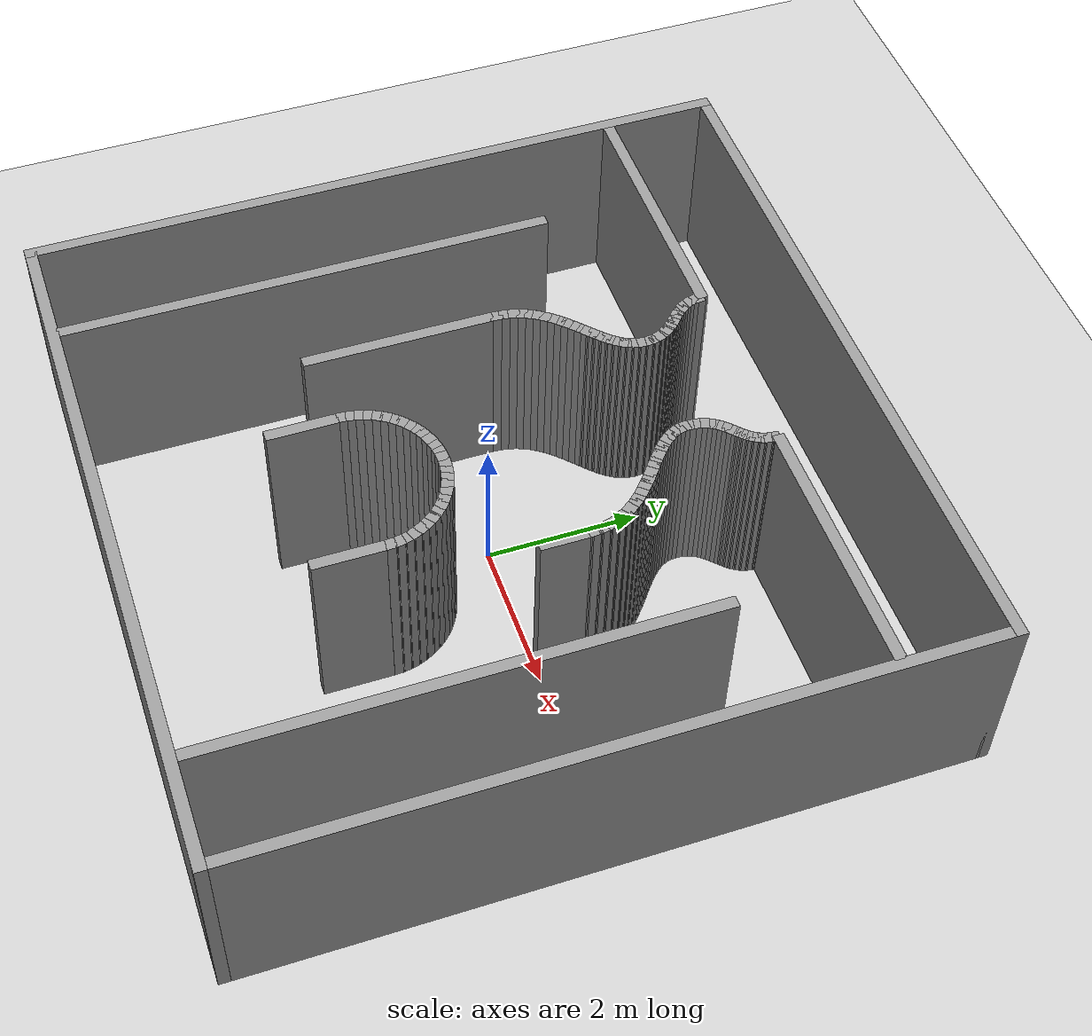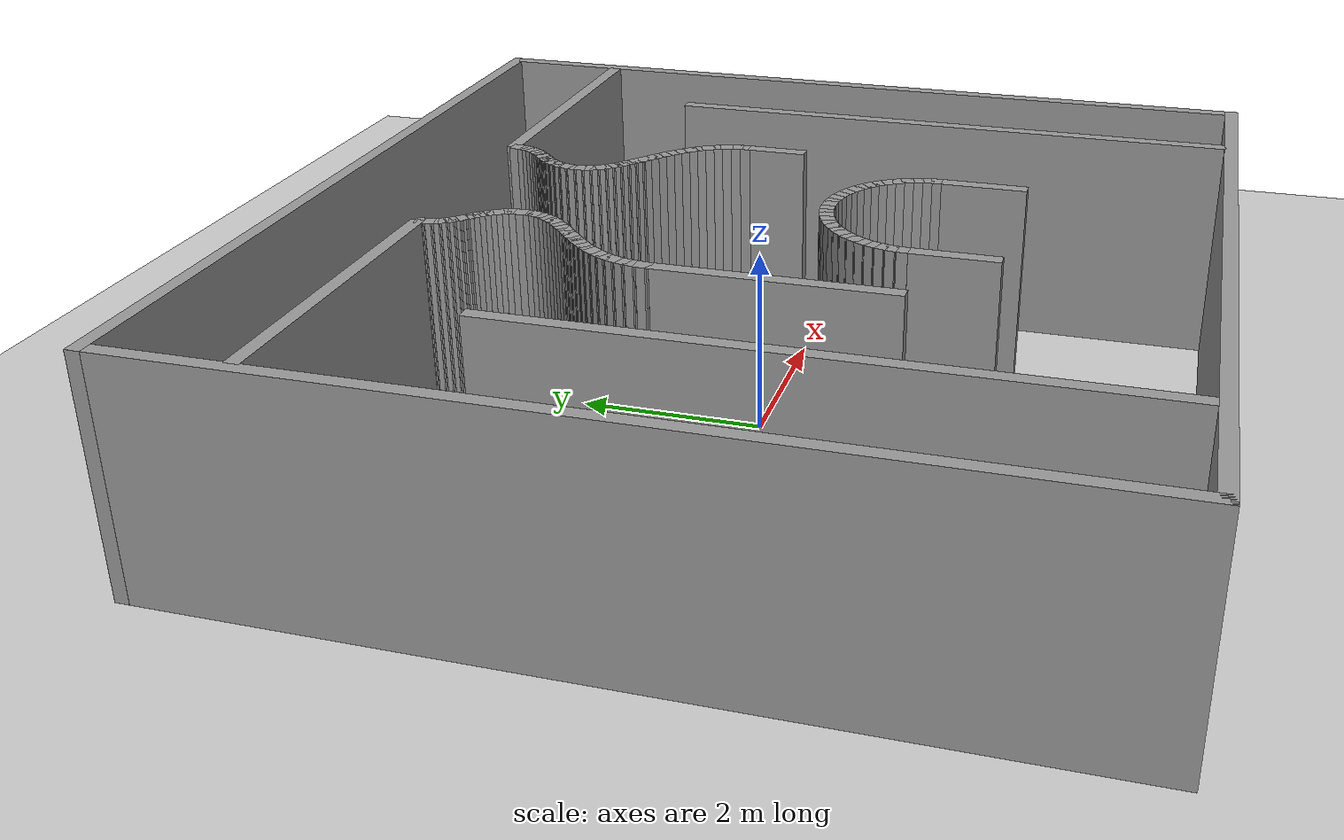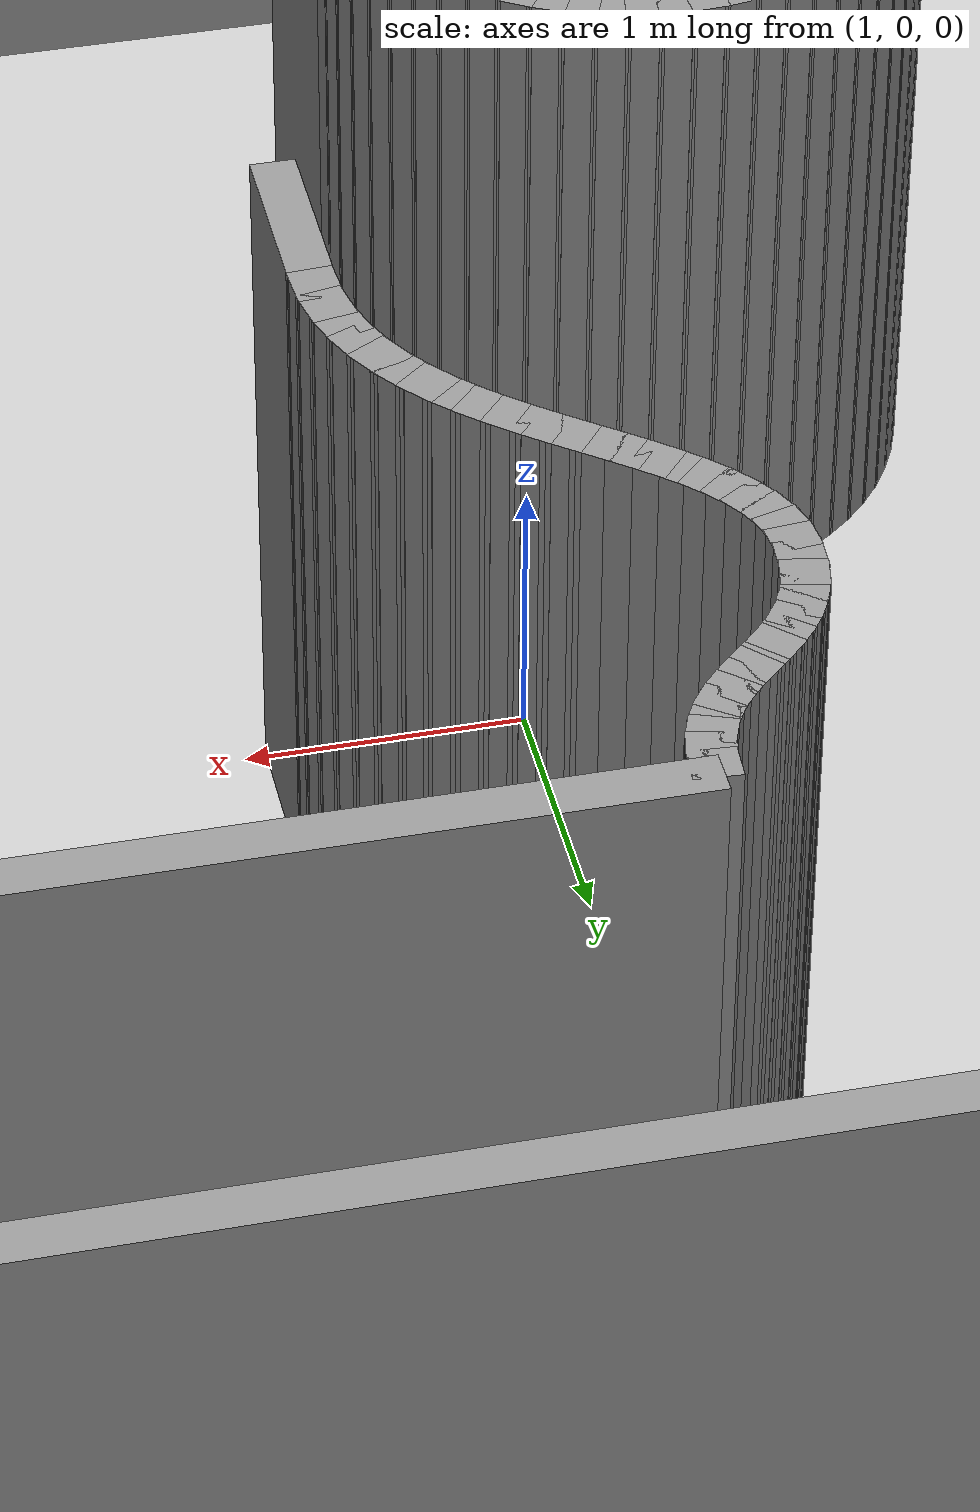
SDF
<sdf version="1.7">
 <world name="default">
  <light name="sun" type="directional">
   <pose>0 0 10 0 -0 0</pose>
   <diffuse>0.8 0.8 0.8 1</diffuse>
   <specular>0.2 0.2 0.2 1</specular>
   <attenuation>
    <range>1000</range>
    <constant>0.9</constant>
    <linear>0.01</linear>
    <quadratic>0.001</quadratic>
   </attenuation>
   <direction>-0.5 0.1 -0.9</direction>
   <spot><inner_angle>0</inner_angle><outer_angle>0</outer_angle><falloff>0</falloff></spot>
  </light>
  <model name="ground_plane">
   <static>1</static>
   <link name="link">
    <collision name="collision">
     <geometry><plane><normal>0 0 1</normal><size>100 100</size></plane></geometry>
     <surface>
      <contact><collide_bitmask>65535</collide_bitmask></contact>
      <friction><ode><mu>100</mu><mu2>50</mu2></ode></friction>
     </surface>
    </collision>
    <visual name="visual">
     <cast_shadows>0</cast_shadows>
     <geometry><plane><normal>0 0 1</normal><size>100 100</size></plane></geometry>
     <material>
      <script><uri>file://media/materials/scripts/gazebo.material</uri><name>Gazebo/Grey</name></script>
     </material>
    </visual>
   </link>
  </model>
  <gravity>0 0 -9.8</gravity>
  <magnetic_field>6e-06 2.3e-05 -4.2e-05</magnetic_field>
  <atmosphere type="adiabatic"/>
  <physics type="ode">
   <max_step_size>0.001</max_step_size>
   <real_time_factor>1</real_time_factor>
   <real_time_update_rate>1000</real_time_update_rate>
  </physics>
  <scene><ambient>0.4 0.4 0.4 1</ambient><background>0.7 0.7 0.7 1</background><shadows>1</shadows></scene>
  <spherical_coordinates>
   <surface_model>EARTH_WGS84</surface_model>
   <latitude_deg>0</latitude_deg>
   <longitude_deg>0</longitude_deg>
   <elevation>0</elevation>
   <heading_deg>0</heading_deg>
  </spherical_coordinates>
  <model name="map_hourglass_u_outer">
   <link name="Wall_bottom">
    <collision name="Wall_bottom_Collision">
     <geometry><box><size>9.35 0.15 2.5</size></box></geometry>
     <pose>0 0 1.25 0 -0 0</pose>
    </collision>
    <visual name="Wall_bottom_Visual">
     <pose>0 0 1.25 0 -0 0</pose>
     <geometry><box><size>9.35 0.15 2.5</size></box></geometry>
     <material>
      <script><uri>file://media/materials/scripts/gazebo.material</uri><name>Gazebo/Grey</name></script>
      <ambient>1 1 1 1</ambient>
     </material>
    </visual>
    <pose>0.000000 -4.600000 0 0 -0 0.000000</pose>
   </link>
   <link name="Wall_top">
    <collision name="Wall_top_Collision">
     <geometry><box><size>9.35 0.15 2.5</size></box></geometry>
     <pose>0 0 1.25 0 -0 0</pose>
    </collision>
    <visual name="Wall_top_Visual">
     <pose>0 0 1.25 0 -0 0</pose>
     <geometry><box><size>9.35 0.15 2.5</size></box></geometry>
     <material>
      <script><uri>file://media/materials/scripts/gazebo.material</uri><name>Gazebo/Grey</name></script>
      <ambient>1 1 1 1</ambient>
     </material>
    </visual>
    <pose>0.000000 4.600000 0 0 -0 0.000000</pose>
   </link>
   <link name="Wall_left">
    <collision name="Wall_left_Collision">
     <geometry><box><size>9.35 0.15 2.5</size></box></geometry>
     <pose>0 0 1.25 0 -0 0</pose>
    </collision>
    <visual name="Wall_left_Visual">
     <pose>0 0 1.25 0 -0 0</pose>
     <geometry><box><size>9.35 0.15 2.5</size></box></geometry>
     <material>
      <script><uri>file://media/materials/scripts/gazebo.material</uri><name>Gazebo/Grey</name></script>
      <ambient>1 1 1 1</ambient>
     </material>
    </visual>
    <pose>-4.600000 0.000000 0 0 -0 1.570796</pose>
   </link>
   <link name="Wall_right">
    <collision name="Wall_right_Collision">
     <geometry><box><size>9.35 0.15 2.5</size></box></geometry>
     <pose>0 0 1.25 0 -0 0</pose>
    </collision>
    <visual name="Wall_right_Visual">
     <pose>0 0 1.25 0 -0 0</pose>
     <geometry><box><size>9.35 0.15 2.5</size></box></geometry>
     <material>
      <script><uri>file://media/materials/scripts/gazebo.material</uri><name>Gazebo/Grey</name></script>
      <ambient>1 1 1 1</ambient>
     </material>
    </visual>
    <pose>4.600000 0.000000 0 0 -0 1.570796</pose>
   </link>
   <static>1</static>
  </model>
  <model name="map_hourglass_u_divider">
   <link name="Divider_left">
    <collision name="Divider_left_Collision">
     <geometry><box><size>3.365 0.15 2.5</size></box></geometry>
     <pose>0 0 1.25 0 -0 0</pose>
    </collision>
    <visual name="Divider_left_Visual">
     <pose>0 0 1.25 0 -0 0</pose>
     <geometry><box><size>3.365 0.15 2.5</size></box></geometry>
     <material>
      <script><uri>file://media/materials/scripts/gazebo.material</uri><name>Gazebo/Grey</name></script>
      <ambient>1 1 1 1</ambient>
     </material>
    </visual>
    <pose>-2.862500 3.200000 0 0 -0 0.000000</pose>
   </link>
   <link name="Divider_right">
    <collision name="Divider_right_Collision">
     <geometry><box><size>3.365 0.15 2.5</size></box></geometry>
     <pose>0 0 1.25 0 -0 0</pose>
    </collision>
    <visual name="Divider_right_Visual">
     <pose>0 0 1.25 0 -0 0</pose>
     <geometry><box><size>3.365 0.15 2.5</size></box></geometry>
     <material>
      <script><uri>file://media/materials/scripts/gazebo.material</uri><name>Gazebo/Grey</name></script>
      <ambient>1 1 1 1</ambient>
     </material>
    </visual>
    <pose>2.862500 3.200000 0 0 -0 0.000000</pose>
   </link>
   <static>1</static>
  </model>
  <model name="map_hourglass_u_hourglass">
   <link name="Hourglass_left_upper_00">
    <collision name="Hourglass_left_upper_00_Collision">
     <geometry><box><size>0.124347 0.15 2.5</size></box></geometry>
     <pose>0 0 1.25 0 -0 0</pose>
    </collision>
    <visual name="Hourglass_left_upper_00_Visual">
     <pose>0 0 1.25 0 -0 0</pose>
     <geometry><box><size>0.124347 0.15 2.5</size></box></geometry>
     <material>
      <script><uri>file://media/materials/scripts/gazebo.material</uri><name>Gazebo/Grey</name></script>
      <ambient>1 1 1 1</ambient>
     </material>
    </visual>
    <pose>-1.197249 3.157916 0 0 -0 -1.505509</pose>
   </link>
   <link name="Hourglass_left_upper_01">
    <collision name="Hourglass_left_upper_01_Collision">
     <geometry><box><size>0.115174 0.15 2.5</size></box></geometry>
     <pose>0 0 1.25 0 -0 0</pose>
    </collision>
    <visual name="Hourglass_left_upper_01_Visual">
     <pose>0 0 1.25 0 -0 0</pose>
     <geometry><box><size>0.115174 0.15 2.5</size></box></geometry>
     <material>
      <script><uri>file://media/materials/scripts/gazebo.material</uri><name>Gazebo/Grey</name></script>
      <ambient>1 1 1 1</ambient>
     </material>
    </visual>
    <pose>-1.186721 3.079059 0 0 -0 -1.362414</pose>
   </link>
   <link name="Hourglass_left_upper_02">
    <collision name="Hourglass_left_upper_02_Collision">
     <geometry><box><size>0.108873 0.15 2.5</size></box></geometry>
     <pose>0 0 1.25 0 -0 0</pose>
    </collision>
    <visual name="Hourglass_left_upper_02_Visual">
     <pose>0 0 1.25 0 -0 0</pose>
     <geometry><box><size>0.108873 0.15 2.5</size></box></geometry>
     <material>
      <script><uri>file://media/materials/scripts/gazebo.material</uri><name>Gazebo/Grey</name></script>
      <ambient>1 1 1 1</ambient>
     </material>
    </visual>
    <pose>-1.166863 3.010038 0 0 -0 -1.212304</pose>
   </link>
   <link name="Hourglass_left_upper_03">
    <collision name="Hourglass_left_upper_03_Collision">
     <geometry><box><size>0.105057 0.15 2.5</size></box></geometry>
     <pose>0 0 1.25 0 -0 0</pose>
    </collision>
    <visual name="Hourglass_left_upper_03_Visual">
     <pose>0 0 1.25 0 -0 0</pose>
     <geometry><box><size>0.105057 0.15 2.5</size></box></geometry>
     <material>
      <script><uri>file://media/materials/scripts/gazebo.material</uri><name>Gazebo/Grey</name></script>
      <ambient>1 1 1 1</ambient>
     </material>
    </visual>
    <pose>-1.139109 2.949286 0 0 -0 -1.068119</pose>
   </link>
   <link name="Hourglass_left_upper_04">
    <collision name="Hourglass_left_upper_04_Collision">
     <geometry><box><size>0.103132 0.15 2.5</size></box></geometry>
     <pose>0 0 1.25 0 -0 0</pose>
    </collision>
    <visual name="Hourglass_left_upper_04_Visual">
     <pose>0 0 1.25 0 -0 0</pose>
     <geometry><box><size>0.103132 0.15 2.5</size></box></geometry>
     <material>
      <script><uri>file://media/materials/scripts/gazebo.material</uri><name>Gazebo/Grey</name></script>
      <ambient>1 1 1 1</ambient>
     </material>
    </visual>
    <pose>-1.104895 2.895236 0 0 -0 -0.942927</pose>
   </link>
   <link name="Hourglass_left_upper_05">
    <collision name="Hourglass_left_upper_05_Collision">
     <geometry><box><size>0.102434 0.15 2.5</size></box></geometry>
     <pose>0 0 1.25 0 -0 0</pose>
    </collision>
    <visual name="Hourglass_left_upper_05_Visual">
     <pose>0 0 1.25 0 -0 0</pose>
     <geometry><box><size>0.102434 0.15 2.5</size></box></geometry>
     <material>
      <script><uri>file://media/materials/scripts/gazebo.material</uri><name>Gazebo/Grey</name></script>
      <ambient>1 1 1 1</ambient>
     </material>
    </visual>
    <pose>-1.065657 2.846320 0 0 -0 -0.846018</pose>
   </link>
   <link name="Hourglass_left_upper_06">
    <collision name="Hourglass_left_upper_06_Collision">
     <geometry><box><size>0.102381 0.15 2.5</size></box></geometry>
     <pose>0 0 1.25 0 -0 0</pose>
    </collision>
    <visual name="Hourglass_left_upper_06_Visual">
     <pose>0 0 1.25 0 -0 0</pose>
     <geometry><box><size>0.102381 0.15 2.5</size></box></geometry>
     <material>
      <script><uri>file://media/materials/scripts/gazebo.material</uri><name>Gazebo/Grey</name></script>
      <ambient>1 1 1 1</ambient>
     </material>
    </visual>
    <pose>-1.022830 2.800970 0 0 -0 -0.781939</pose>
   </link>
   <link name="Hourglass_left_upper_07">
    <collision name="Hourglass_left_upper_07_Collision">
     <geometry><box><size>0.102571 0.15 2.5</size></box></geometry>
     <pose>0 0 1.25 0 -0 0</pose>
    </collision>
    <visual name="Hourglass_left_upper_07_Visual">
     <pose>0 0 1.25 0 -0 0</pose>
     <geometry><box><size>0.102571 0.15 2.5</size></box></geometry>
     <material>
      <script><uri>file://media/materials/scripts/gazebo.material</uri><name>Gazebo/Grey</name></script>
      <ambient>1 1 1 1</ambient>
     </material>
    </visual>
    <pose>-0.977849 2.757621 0 0 -0 -0.751981</pose>
   </link>
   <link name="Hourglass_left_upper_08">
    <collision name="Hourglass_left_upper_08_Collision">
     <geometry><box><size>0.102812 0.15 2.5</size></box></geometry>
     <pose>0 0 1.25 0 -0 0</pose>
    </collision>
    <visual name="Hourglass_left_upper_08_Visual">
     <pose>0 0 1.25 0 -0 0</pose>
     <geometry><box><size>0.102812 0.15 2.5</size></box></geometry>
     <material>
      <script><uri>file://media/materials/scripts/gazebo.material</uri><name>Gazebo/Grey</name></script>
      <ambient>1 1 1 1</ambient>
     </material>
    </visual>
    <pose>-0.932151 2.714703 0 0 -0 -0.756068</pose>
   </link>
   <link name="Hourglass_left_upper_09">
    <collision name="Hourglass_left_upper_09_Collision">
     <geometry><box><size>0.103129 0.15 2.5</size></box></geometry>
     <pose>0 0 1.25 0 -0 0</pose>
    </collision>
    <visual name="Hourglass_left_upper_09_Visual">
     <pose>0 0 1.25 0 -0 0</pose>
     <geometry><box><size>0.103129 0.15 2.5</size></box></geometry>
     <material>
      <script><uri>file://media/materials/scripts/gazebo.material</uri><name>Gazebo/Grey</name></script>
      <ambient>1 1 1 1</ambient>
     </material>
    </visual>
    <pose>-0.887170 2.670651 0 0 -0 -0.793794</pose>
   </link>
   <link name="Hourglass_left_upper_10">
    <collision name="Hourglass_left_upper_10_Collision">
     <geometry><box><size>0.10376 0.15 2.5</size></box></geometry>
     <pose>0 0 1.25 0 -0 0</pose>
    </collision>
    <visual name="Hourglass_left_upper_10_Visual">
     <pose>0 0 1.25 0 -0 0</pose>
     <geometry><box><size>0.10376 0.15 2.5</size></box></geometry>
     <material>
      <script><uri>file://media/materials/scripts/gazebo.material</uri><name>Gazebo/Grey</name></script>
      <ambient>1 1 1 1</ambient>
     </material>
    </visual>
    <pose>-0.844343 2.623895 0 0 -0 -0.864296</pose>
   </link>
   <link name="Hourglass_left_upper_11">
    <collision name="Hourglass_left_upper_11_Collision">
     <geometry><box><size>0.105139 0.15 2.5</size></box></geometry>
     <pose>0 0 1.25 0 -0 0</pose>
    </collision>
    <visual name="Hourglass_left_upper_11_Visual">
     <pose>0 0 1.25 0 -0 0</pose>
     <geometry><box><size>0.105139 0.15 2.5</size></box></geometry>
     <material>
      <script><uri>file://media/materials/scripts/gazebo.material</uri><name>Gazebo/Grey</name></script>
      <ambient>1 1 1 1</ambient>
     </material>
    </visual>
    <pose>-0.805105 2.572870 0 0 -0 -0.965121</pose>
   </link>
   <link name="Hourglass_left_upper_12">
    <collision name="Hourglass_left_upper_12_Collision">
     <geometry><box><size>0.107847 0.15 2.5</size></box></geometry>
     <pose>0 0 1.25 0 -0 0</pose>
    </collision>
    <visual name="Hourglass_left_upper_12_Visual">
     <pose>0 0 1.25 0 -0 0</pose>
     <geometry><box><size>0.107847 0.15 2.5</size></box></geometry>
     <material>
      <script><uri>file://media/materials/scripts/gazebo.material</uri><name>Gazebo/Grey</name></script>
      <ambient>1 1 1 1</ambient>
     </material>
    </visual>
    <pose>-0.770891 2.516007 0 0 -0 -1.090589</pose>
   </link>
   <link name="Hourglass_left_upper_13">
    <collision name="Hourglass_left_upper_13_Collision">
     <geometry><box><size>0.112507 0.15 2.5</size></box></geometry>
     <pose>0 0 1.25 0 -0 0</pose>
    </collision>
    <visual name="Hourglass_left_upper_13_Visual">
     <pose>0 0 1.25 0 -0 0</pose>
     <geometry><box><size>0.112507 0.15 2.5</size></box></geometry>
     <material>
      <script><uri>file://media/materials/scripts/gazebo.material</uri><name>Gazebo/Grey</name></script>
      <ambient>1 1 1 1</ambient>
     </material>
    </visual>
    <pose>-0.743137 2.451740 0 0 -0 -1.231018</pose>
   </link>
   <link name="Hourglass_left_upper_14">
    <collision name="Hourglass_left_upper_14_Collision">
     <geometry><box><size>0.119651 0.15 2.5</size></box></geometry>
     <pose>0 0 1.25 0 -0 0</pose>
    </collision>
    <visual name="Hourglass_left_upper_14_Visual">
     <pose>0 0 1.25 0 -0 0</pose>
     <geometry><box><size>0.119651 0.15 2.5</size></box></geometry>
     <material>
      <script><uri>file://media/materials/scripts/gazebo.material</uri><name>Gazebo/Grey</name></script>
      <ambient>1 1 1 1</ambient>
     </material>
    </visual>
    <pose>-0.723279 2.378500 0 0 -0 -1.374284</pose>
   </link>
   <link name="Hourglass_left_upper_15">
    <collision name="Hourglass_left_upper_15_Collision">
     <geometry><box><size>0.12961 0.15 2.5</size></box></geometry>
     <pose>0 0 1.25 0 -0 0</pose>
    </collision>
    <visual name="Hourglass_left_upper_15_Visual">
     <pose>0 0 1.25 0 -0 0</pose>
     <geometry><box><size>0.12961 0.15 2.5</size></box></geometry>
     <material>
      <script><uri>file://media/materials/scripts/gazebo.material</uri><name>Gazebo/Grey</name></script>
      <ambient>1 1 1 1</ambient>
     </material>
    </visual>
    <pose>-0.712751 2.294720 0 0 -0 -1.509348</pose>
   </link>
   <link name="Hourglass_left_lower_00">
    <collision name="Hourglass_left_lower_00_Collision">
     <geometry><box><size>0.115649 0.15 2.5</size></box></geometry>
     <pose>0 0 1.25 0 -0 0</pose>
    </collision>
    <visual name="Hourglass_left_lower_00_Visual">
     <pose>0 0 1.25 0 -0 0</pose>
     <geometry><box><size>0.115649 0.15 2.5</size></box></geometry>
     <material>
      <script><uri>file://media/materials/scripts/gazebo.material</uri><name>Gazebo/Grey</name></script>
      <ambient>1 1 1 1</ambient>
     </material>
    </visual>
    <pose>-0.712975 2.212293 0 0 -0 -1.649536</pose>
   </link>
   <link name="Hourglass_left_lower_01">
    <collision name="Hourglass_left_lower_01_Collision">
     <geometry><box><size>0.113231 0.15 2.5</size></box></geometry>
     <pose>0 0 1.25 0 -0 0</pose>
    </collision>
    <visual name="Hourglass_left_lower_01_Visual">
     <pose>0 0 1.25 0 -0 0</pose>
     <geometry><box><size>0.113231 0.15 2.5</size></box></geometry>
     <material>
      <script><uri>file://media/materials/scripts/gazebo.material</uri><name>Gazebo/Grey</name></script>
      <ambient>1 1 1 1</ambient>
     </material>
    </visual>
    <pose>-0.724504 2.138983 0 0 -0 -1.806584</pose>
   </link>
   <link name="Hourglass_left_lower_02">
    <collision name="Hourglass_left_lower_02_Collision">
     <geometry><box><size>0.112868 0.15 2.5</size></box></geometry>
     <pose>0 0 1.25 0 -0 0</pose>
    </collision>
    <visual name="Hourglass_left_lower_02_Visual">
     <pose>0 0 1.25 0 -0 0</pose>
     <geometry><box><size>0.112868 0.15 2.5</size></box></geometry>
     <material>
      <script><uri>file://media/materials/scripts/gazebo.material</uri><name>Gazebo/Grey</name></script>
      <ambient>1 1 1 1</ambient>
     </material>
    </visual>
    <pose>-0.746632 2.069570 0 0 -0 -1.952581</pose>
   </link>
   <link name="Hourglass_left_lower_03">
    <collision name="Hourglass_left_lower_03_Collision">
     <geometry><box><size>0.114045 0.15 2.5</size></box></geometry>
     <pose>0 0 1.25 0 -0 0</pose>
    </collision>
    <visual name="Hourglass_left_lower_03_Visual">
     <pose>0 0 1.25 0 -0 0</pose>
     <geometry><box><size>0.114045 0.15 2.5</size></box></geometry>
     <material>
      <script><uri>file://media/materials/scripts/gazebo.material</uri><name>Gazebo/Grey</name></script>
      <ambient>1 1 1 1</ambient>
     </material>
    </visual>
    <pose>-0.778244 2.003428 0 0 -0 -2.079672</pose>
   </link>
   <link name="Hourglass_left_lower_04">
    <collision name="Hourglass_left_lower_04_Collision">
     <geometry><box><size>0.116229 0.15 2.5</size></box></geometry>
     <pose>0 0 1.25 0 -0 0</pose>
    </collision>
    <visual name="Hourglass_left_lower_04_Visual">
     <pose>0 0 1.25 0 -0 0</pose>
     <geometry><box><size>0.116229 0.15 2.5</size></box></geometry>
     <material>
      <script><uri>file://media/materials/scripts/gazebo.material</uri><name>Gazebo/Grey</name></script>
      <ambient>1 1 1 1</ambient>
     </material>
    </visual>
    <pose>-0.818223 1.939932 0 0 -0 -2.184244</pose>
   </link>
   <link name="Hourglass_left_lower_05">
    <collision name="Hourglass_left_lower_05_Collision">
     <geometry><box><size>0.118951 0.15 2.5</size></box></geometry>
     <pose>0 0 1.25 0 -0 0</pose>
    </collision>
    <visual name="Hourglass_left_lower_05_Visual">
     <pose>0 0 1.25 0 -0 0</pose>
     <geometry><box><size>0.118951 0.15 2.5</size></box></geometry>
     <material>
      <script><uri>file://media/materials/scripts/gazebo.material</uri><name>Gazebo/Grey</name></script>
      <ambient>1 1 1 1</ambient>
     </material>
    </visual>
    <pose>-0.865455 1.878456 0 0 -0 -2.266115</pose>
   </link>
   <link name="Hourglass_left_lower_06">
    <collision name="Hourglass_left_lower_06_Collision">
     <geometry><box><size>0.121846 0.15 2.5</size></box></geometry>
     <pose>0 0 1.25 0 -0 0</pose>
    </collision>
    <visual name="Hourglass_left_lower_06_Visual">
     <pose>0 0 1.25 0 -0 0</pose>
     <geometry><box><size>0.121846 0.15 2.5</size></box></geometry>
     <material>
      <script><uri>file://media/materials/scripts/gazebo.material</uri><name>Gazebo/Grey</name></script>
      <ambient>1 1 1 1</ambient>
     </material>
    </visual>
    <pose>-0.918822 1.818374 0 0 -0 -2.326957</pose>
   </link>
   <link name="Hourglass_left_lower_07">
    <collision name="Hourglass_left_lower_07_Collision">
     <geometry><box><size>0.124651 0.15 2.5</size></box></geometry>
     <pose>0 0 1.25 0 -0 0</pose>
    </collision>
    <visual name="Hourglass_left_lower_07_Visual">
     <pose>0 0 1.25 0 -0 0</pose>
     <geometry><box><size>0.124651 0.15 2.5</size></box></geometry>
     <material>
      <script><uri>file://media/materials/scripts/gazebo.material</uri><name>Gazebo/Grey</name></script>
      <ambient>1 1 1 1</ambient>
     </material>
    </visual>
    <pose>-0.977211 1.759061 0 0 -0 -2.369021</pose>
   </link>
   <link name="Hourglass_left_lower_08">
    <collision name="Hourglass_left_lower_08_Collision">
     <geometry><box><size>0.127194 0.15 2.5</size></box></geometry>
     <pose>0 0 1.25 0 -0 0</pose>
    </collision>
    <visual name="Hourglass_left_lower_08_Visual">
     <pose>0 0 1.25 0 -0 0</pose>
     <geometry><box><size>0.127194 0.15 2.5</size></box></geometry>
     <material>
      <script><uri>file://media/materials/scripts/gazebo.material</uri><name>Gazebo/Grey</name></script>
      <ambient>1 1 1 1</ambient>
     </material>
    </visual>
    <pose>-1.039504 1.699892 0 0 -0 -2.394429</pose>
   </link>
   <link name="Hourglass_left_lower_09">
    <collision name="Hourglass_left_lower_09_Collision">
     <geometry><box><size>0.129375 0.15 2.5</size></box></geometry>
     <pose>0 0 1.25 0 -0 0</pose>
    </collision>
    <visual name="Hourglass_left_lower_09_Visual">
     <pose>0 0 1.25 0 -0 0</pose>
     <geometry><box><size>0.129375 0.15 2.5</size></box></geometry>
     <material>
      <script><uri>file://media/materials/scripts/gazebo.material</uri><name>Gazebo/Grey</name></script>
      <ambient>1 1 1 1</ambient>
     </material>
    </visual>
    <pose>-1.104587 1.640242 0 0 -0 -2.404874</pose>
   </link>
   <link name="Hourglass_left_lower_10">
    <collision name="Hourglass_left_lower_10_Collision">
     <geometry><box><size>0.131156 0.15 2.5</size></box></geometry>
     <pose>0 0 1.25 0 -0 0</pose>
    </collision>
    <visual name="Hourglass_left_lower_10_Visual">
     <pose>0 0 1.25 0 -0 0</pose>
     <geometry><box><size>0.131156 0.15 2.5</size></box></geometry>
     <material>
      <script><uri>file://media/materials/scripts/gazebo.material</uri><name>Gazebo/Grey</name></script>
      <ambient>1 1 1 1</ambient>
     </material>
    </visual>
    <pose>-1.171343 1.579484 0 0 -0 -2.401559</pose>
   </link>
   <link name="Hourglass_left_lower_11">
    <collision name="Hourglass_left_lower_11_Collision">
     <geometry><box><size>0.132548 0.15 2.5</size></box></geometry>
     <pose>0 0 1.25 0 -0 0</pose>
    </collision>
    <visual name="Hourglass_left_lower_11_Visual">
     <pose>0 0 1.25 0 -0 0</pose>
     <geometry><box><size>0.132548 0.15 2.5</size></box></geometry>
     <material>
      <script><uri>file://media/materials/scripts/gazebo.material</uri><name>Gazebo/Grey</name></script>
      <ambient>1 1 1 1</ambient>
     </material>
    </visual>
    <pose>-1.238657 1.516993 0 0 -0 -2.385238</pose>
   </link>
   <link name="Hourglass_left_lower_12">
    <collision name="Hourglass_left_lower_12_Collision">
     <geometry><box><size>0.133609 0.15 2.5</size></box></geometry>
     <pose>0 0 1.25 0 -0 0</pose>
    </collision>
    <visual name="Hourglass_left_lower_12_Visual">
     <pose>0 0 1.25 0 -0 0</pose>
     <geometry><box><size>0.133609 0.15 2.5</size></box></geometry>
     <material>
      <script><uri>file://media/materials/scripts/gazebo.material</uri><name>Gazebo/Grey</name></script>
      <ambient>1 1 1 1</ambient>
     </material>
    </visual>
    <pose>-1.305413 1.452145 0 0 -0 -2.356301</pose>
   </link>
   <link name="Hourglass_left_lower_13">
    <collision name="Hourglass_left_lower_13_Collision">
     <geometry><box><size>0.134442 0.15 2.5</size></box></geometry>
     <pose>0 0 1.25 0 -0 0</pose>
    </collision>
    <visual name="Hourglass_left_lower_13_Visual">
     <pose>0 0 1.25 0 -0 0</pose>
     <geometry><box><size>0.134442 0.15 2.5</size></box></geometry>
     <material>
      <script><uri>file://media/materials/scripts/gazebo.material</uri><name>Gazebo/Grey</name></script>
      <ambient>1 1 1 1</ambient>
     </material>
    </visual>
    <pose>-1.370496 1.384312 0 0 -0 -2.314901</pose>
   </link>
   <link name="Hourglass_left_lower_14">
    <collision name="Hourglass_left_lower_14_Collision">
     <geometry><box><size>0.135198 0.15 2.5</size></box></geometry>
     <pose>0 0 1.25 0 -0 0</pose>
    </collision>
    <visual name="Hourglass_left_lower_14_Visual">
     <pose>0 0 1.25 0 -0 0</pose>
     <geometry><box><size>0.135198 0.15 2.5</size></box></geometry>
     <material>
      <script><uri>file://media/materials/scripts/gazebo.material</uri><name>Gazebo/Grey</name></script>
      <ambient>1 1 1 1</ambient>
     </material>
    </visual>
    <pose>-1.432789 1.312870 0 0 -0 -2.261105</pose>
   </link>
   <link name="Hourglass_left_lower_15">
    <collision name="Hourglass_left_lower_15_Collision">
     <geometry><box><size>0.136072 0.15 2.5</size></box></geometry>
     <pose>0 0 1.25 0 -0 0</pose>
    </collision>
    <visual name="Hourglass_left_lower_15_Visual">
     <pose>0 0 1.25 0 -0 0</pose>
     <geometry><box><size>0.136072 0.15 2.5</size></box></geometry>
     <material>
      <script><uri>file://media/materials/scripts/gazebo.material</uri><name>Gazebo/Grey</name></script>
      <ambient>1 1 1 1</ambient>
     </material>
    </visual>
    <pose>-1.491178 1.237194 0 0 -0 -2.195099</pose>
   </link>
   <link name="Hourglass_left_lower_16">
    <collision name="Hourglass_left_lower_16_Collision">
     <geometry><box><size>0.137301 0.15 2.5</size></box></geometry>
     <pose>0 0 1.25 0 -0 0</pose>
    </collision>
    <visual name="Hourglass_left_lower_16_Visual">
     <pose>0 0 1.25 0 -0 0</pose>
     <geometry><box><size>0.137301 0.15 2.5</size></box></geometry>
     <material>
      <script><uri>file://media/materials/scripts/gazebo.material</uri><name>Gazebo/Grey</name></script>
      <ambient>1 1 1 1</ambient>
     </material>
    </visual>
    <pose>-1.544545 1.156658 0 0 -0 -2.117428</pose>
   </link>
   <link name="Hourglass_left_lower_17">
    <collision name="Hourglass_left_lower_17_Collision">
     <geometry><box><size>0.13916 0.15 2.5</size></box></geometry>
     <pose>0 0 1.25 0 -0 0</pose>
    </collision>
    <visual name="Hourglass_left_lower_17_Visual">
     <pose>0 0 1.25 0 -0 0</pose>
     <geometry><box><size>0.13916 0.15 2.5</size></box></geometry>
     <material>
      <script><uri>file://media/materials/scripts/gazebo.material</uri><name>Gazebo/Grey</name></script>
      <ambient>1 1 1 1</ambient>
     </material>
    </visual>
    <pose>-1.591777 1.070636 0 0 -0 -2.029247</pose>
   </link>
   <link name="Hourglass_left_lower_18">
    <collision name="Hourglass_left_lower_18_Collision">
     <geometry><box><size>0.141941 0.15 2.5</size></box></geometry>
     <pose>0 0 1.25 0 -0 0</pose>
    </collision>
    <visual name="Hourglass_left_lower_18_Visual">
     <pose>0 0 1.25 0 -0 0</pose>
     <geometry><box><size>0.141941 0.15 2.5</size></box></geometry>
     <material>
      <script><uri>file://media/materials/scripts/gazebo.material</uri><name>Gazebo/Grey</name></script>
      <ambient>1 1 1 1</ambient>
     </material>
    </visual>
    <pose>-1.631756 0.978503 0 0 -0 -1.932507</pose>
   </link>
   <link name="Hourglass_left_lower_19">
    <collision name="Hourglass_left_lower_19_Collision">
     <geometry><box><size>0.145932 0.15 2.5</size></box></geometry>
     <pose>0 0 1.25 0 -0 0</pose>
    </collision>
    <visual name="Hourglass_left_lower_19_Visual">
     <pose>0 0 1.25 0 -0 0</pose>
     <geometry><box><size>0.145932 0.15 2.5</size></box></geometry>
     <material>
      <script><uri>file://media/materials/scripts/gazebo.material</uri><name>Gazebo/Grey</name></script>
      <ambient>1 1 1 1</ambient>
     </material>
    </visual>
    <pose>-1.663368 0.879634 0 0 -0 -1.829973</pose>
   </link>
   <link name="Hourglass_left_lower_20">
    <collision name="Hourglass_left_lower_20_Collision">
     <geometry><box><size>0.15139 0.15 2.5</size></box></geometry>
     <pose>0 0 1.25 0 -0 0</pose>
    </collision>
    <visual name="Hourglass_left_lower_20_Visual">
     <pose>0 0 1.25 0 -0 0</pose>
     <geometry><box><size>0.15139 0.15 2.5</size></box></geometry>
     <material>
      <script><uri>file://media/materials/scripts/gazebo.material</uri><name>Gazebo/Grey</name></script>
      <ambient>1 1 1 1</ambient>
     </material>
    </visual>
    <pose>-1.685496 0.773403 0 0 -0 -1.724988</pose>
   </link>
   <link name="Hourglass_left_lower_21">
    <collision name="Hourglass_left_lower_21_Collision">
     <geometry><box><size>0.158518 0.15 2.5</size></box></geometry>
     <pose>0 0 1.25 0 -0 0</pose>
    </collision>
    <visual name="Hourglass_left_lower_21_Visual">
     <pose>0 0 1.25 0 -0 0</pose>
     <geometry><box><size>0.158518 0.15 2.5</size></box></geometry>
     <material>
      <script><uri>file://media/materials/scripts/gazebo.material</uri><name>Gazebo/Grey</name></script>
      <ambient>1 1 1 1</ambient>
     </material>
    </visual>
    <pose>-1.697025 0.659184 0 0 -0 -1.621024</pose>
   </link>
   <link name="Hourglass_left_arm">
    <collision name="Hourglass_left_arm_Collision">
     <geometry><box><size>2.44 0.15 2.5</size></box></geometry>
     <pose>0 0 1.25 0 -0 0</pose>
    </collision>
    <visual name="Hourglass_left_arm_Visual">
     <pose>0 0 1.25 0 -0 0</pose>
     <geometry><box><size>2.44 0.15 2.5</size></box></geometry>
     <material>
      <script><uri>file://media/materials/scripts/gazebo.material</uri><name>Gazebo/Grey</name></script>
      <ambient>1 1 1 1</ambient>
     </material>
    </visual>
    <pose>-1.700000 -0.600000 0 0 -0 -1.570796</pose>
   </link>
   <link name="Hourglass_right_upper_00">
    <collision name="Hourglass_right_upper_00_Collision">
     <geometry><box><size>0.124347 0.15 2.5</size></box></geometry>
     <pose>0 0 1.25 0 -0 0</pose>
    </collision>
    <visual name="Hourglass_right_upper_00_Visual">
     <pose>0 0 1.25 0 -0 0</pose>
     <geometry><box><size>0.124347 0.15 2.5</size></box></geometry>
     <material>
      <script><uri>file://media/materials/scripts/gazebo.material</uri><name>Gazebo/Grey</name></script>
      <ambient>1 1 1 1</ambient>
     </material>
    </visual>
    <pose>1.197249 3.157916 0 0 -0 -1.636084</pose>
   </link>
   <link name="Hourglass_right_upper_01">
    <collision name="Hourglass_right_upper_01_Collision">
     <geometry><box><size>0.115174 0.15 2.5</size></box></geometry>
     <pose>0 0 1.25 0 -0 0</pose>
    </collision>
    <visual name="Hourglass_right_upper_01_Visual">
     <pose>0 0 1.25 0 -0 0</pose>
     <geometry><box><size>0.115174 0.15 2.5</size></box></geometry>
     <material>
      <script><uri>file://media/materials/scripts/gazebo.material</uri><name>Gazebo/Grey</name></script>
      <ambient>1 1 1 1</ambient>
     </material>
    </visual>
    <pose>1.186721 3.079059 0 0 -0 -1.779179</pose>
   </link>
   <link name="Hourglass_right_upper_02">
    <collision name="Hourglass_right_upper_02_Collision">
     <geometry><box><size>0.108873 0.15 2.5</size></box></geometry>
     <pose>0 0 1.25 0 -0 0</pose>
    </collision>
    <visual name="Hourglass_right_upper_02_Visual">
     <pose>0 0 1.25 0 -0 0</pose>
     <geometry><box><size>0.108873 0.15 2.5</size></box></geometry>
     <material>
      <script><uri>file://media/materials/scripts/gazebo.material</uri><name>Gazebo/Grey</name></script>
      <ambient>1 1 1 1</ambient>
     </material>
    </visual>
    <pose>1.166863 3.010038 0 0 -0 -1.929289</pose>
   </link>
   <link name="Hourglass_right_upper_03">
    <collision name="Hourglass_right_upper_03_Collision">
     <geometry><box><size>0.105057 0.15 2.5</size></box></geometry>
     <pose>0 0 1.25 0 -0 0</pose>
    </collision>
    <visual name="Hourglass_right_upper_03_Visual">
     <pose>0 0 1.25 0 -0 0</pose>
     <geometry><box><size>0.105057 0.15 2.5</size></box></geometry>
     <material>
      <script><uri>file://media/materials/scripts/gazebo.material</uri><name>Gazebo/Grey</name></script>
      <ambient>1 1 1 1</ambient>
     </material>
    </visual>
    <pose>1.139109 2.949286 0 0 -0 -2.073473</pose>
   </link>
   <link name="Hourglass_right_upper_04">
    <collision name="Hourglass_right_upper_04_Collision">
     <geometry><box><size>0.103132 0.15 2.5</size></box></geometry>
     <pose>0 0 1.25 0 -0 0</pose>
    </collision>
    <visual name="Hourglass_right_upper_04_Visual">
     <pose>0 0 1.25 0 -0 0</pose>
     <geometry><box><size>0.103132 0.15 2.5</size></box></geometry>
     <material>
      <script><uri>file://media/materials/scripts/gazebo.material</uri><name>Gazebo/Grey</name></script>
      <ambient>1 1 1 1</ambient>
     </material>
    </visual>
    <pose>1.104895 2.895236 0 0 -0 -2.198666</pose>
   </link>
   <link name="Hourglass_right_upper_05">
    <collision name="Hourglass_right_upper_05_Collision">
     <geometry><box><size>0.102434 0.15 2.5</size></box></geometry>
     <pose>0 0 1.25 0 -0 0</pose>
    </collision>
    <visual name="Hourglass_right_upper_05_Visual">
     <pose>0 0 1.25 0 -0 0</pose>
     <geometry><box><size>0.102434 0.15 2.5</size></box></geometry>
     <material>
      <script><uri>file://media/materials/scripts/gazebo.material</uri><name>Gazebo/Grey</name></script>
      <ambient>1 1 1 1</ambient>
     </material>
    </visual>
    <pose>1.065657 2.846320 0 0 -0 -2.295575</pose>
   </link>
   <link name="Hourglass_right_upper_06">
    <collision name="Hourglass_right_upper_06_Collision">
     <geometry><box><size>0.102381 0.15 2.5</size></box></geometry>
     <pose>0 0 1.25 0 -0 0</pose>
    </collision>
    <visual name="Hourglass_right_upper_06_Visual">
     <pose>0 0 1.25 0 -0 0</pose>
     <geometry><box><size>0.102381 0.15 2.5</size></box></geometry>
     <material>
      <script><uri>file://media/materials/scripts/gazebo.material</uri><name>Gazebo/Grey</name></script>
      <ambient>1 1 1 1</ambient>
     </material>
    </visual>
    <pose>1.022830 2.800970 0 0 -0 -2.359654</pose>
   </link>
   <link name="Hourglass_right_upper_07">
    <collision name="Hourglass_right_upper_07_Collision">
     <geometry><box><size>0.102571 0.15 2.5</size></box></geometry>
     <pose>0 0 1.25 0 -0 0</pose>
    </collision>
    <visual name="Hourglass_right_upper_07_Visual">
     <pose>0 0 1.25 0 -0 0</pose>
     <geometry><box><size>0.102571 0.15 2.5</size></box></geometry>
     <material>
      <script><uri>file://media/materials/scripts/gazebo.material</uri><name>Gazebo/Grey</name></script>
      <ambient>1 1 1 1</ambient>
     </material>
    </visual>
    <pose>0.977849 2.757621 0 0 -0 -2.389612</pose>
   </link>
   <link name="Hourglass_right_upper_08">
    <collision name="Hourglass_right_upper_08_Collision">
     <geometry><box><size>0.102812 0.15 2.5</size></box></geometry>
     <pose>0 0 1.25 0 -0 0</pose>
    </collision>
    <visual name="Hourglass_right_upper_08_Visual">
     <pose>0 0 1.25 0 -0 0</pose>
     <geometry><box><size>0.102812 0.15 2.5</size></box></geometry>
     <material>
      <script><uri>file://media/materials/scripts/gazebo.material</uri><name>Gazebo/Grey</name></script>
      <ambient>1 1 1 1</ambient>
     </material>
    </visual>
    <pose>0.932151 2.714703 0 0 -0 -2.385524</pose>
   </link>
   <link name="Hourglass_right_upper_09">
    <collision name="Hourglass_right_upper_09_Collision">
     <geometry><box><size>0.103129 0.15 2.5</size></box></geometry>
     <pose>0 0 1.25 0 -0 0</pose>
    </collision>
    <visual name="Hourglass_right_upper_09_Visual">
     <pose>0 0 1.25 0 -0 0</pose>
     <geometry><box><size>0.103129 0.15 2.5</size></box></geometry>
     <material>
      <script><uri>file://media/materials/scripts/gazebo.material</uri><name>Gazebo/Grey</name></script>
      <ambient>1 1 1 1</ambient>
     </material>
    </visual>
    <pose>0.887170 2.670651 0 0 -0 -2.347799</pose>
   </link>
   <link name="Hourglass_right_upper_10">
    <collision name="Hourglass_right_upper_10_Collision">
     <geometry><box><size>0.10376 0.15 2.5</size></box></geometry>
     <pose>0 0 1.25 0 -0 0</pose>
    </collision>
    <visual name="Hourglass_right_upper_10_Visual">
     <pose>0 0 1.25 0 -0 0</pose>
     <geometry><box><size>0.10376 0.15 2.5</size></box></geometry>
     <material>
      <script><uri>file://media/materials/scripts/gazebo.material</uri><name>Gazebo/Grey</name></script>
      <ambient>1 1 1 1</ambient>
     </material>
    </visual>
    <pose>0.844343 2.623895 0 0 -0 -2.277296</pose>
   </link>
   <link name="Hourglass_right_upper_11">
    <collision name="Hourglass_right_upper_11_Collision">
     <geometry><box><size>0.105139 0.15 2.5</size></box></geometry>
     <pose>0 0 1.25 0 -0 0</pose>
    </collision>
    <visual name="Hourglass_right_upper_11_Visual">
     <pose>0 0 1.25 0 -0 0</pose>
     <geometry><box><size>0.105139 0.15 2.5</size></box></geometry>
     <material>
      <script><uri>file://media/materials/scripts/gazebo.material</uri><name>Gazebo/Grey</name></script>
      <ambient>1 1 1 1</ambient>
     </material>
    </visual>
    <pose>0.805105 2.572870 0 0 -0 -2.176471</pose>
   </link>
   <link name="Hourglass_right_upper_12">
    <collision name="Hourglass_right_upper_12_Collision">
     <geometry><box><size>0.107847 0.15 2.5</size></box></geometry>
     <pose>0 0 1.25 0 -0 0</pose>
    </collision>
    <visual name="Hourglass_right_upper_12_Visual">
     <pose>0 0 1.25 0 -0 0</pose>
     <geometry><box><size>0.107847 0.15 2.5</size></box></geometry>
     <material>
      <script><uri>file://media/materials/scripts/gazebo.material</uri><name>Gazebo/Grey</name></script>
      <ambient>1 1 1 1</ambient>
     </material>
    </visual>
    <pose>0.770891 2.516007 0 0 -0 -2.051004</pose>
   </link>
   <link name="Hourglass_right_upper_13">
    <collision name="Hourglass_right_upper_13_Collision">
     <geometry><box><size>0.112507 0.15 2.5</size></box></geometry>
     <pose>0 0 1.25 0 -0 0</pose>
    </collision>
    <visual name="Hourglass_right_upper_13_Visual">
     <pose>0 0 1.25 0 -0 0</pose>
     <geometry><box><size>0.112507 0.15 2.5</size></box></geometry>
     <material>
      <script><uri>file://media/materials/scripts/gazebo.material</uri><name>Gazebo/Grey</name></script>
      <ambient>1 1 1 1</ambient>
     </material>
    </visual>
    <pose>0.743137 2.451740 0 0 -0 -1.910575</pose>
   </link>
   <link name="Hourglass_right_upper_14">
    <collision name="Hourglass_right_upper_14_Collision">
     <geometry><box><size>0.119651 0.15 2.5</size></box></geometry>
     <pose>0 0 1.25 0 -0 0</pose>
    </collision>
    <visual name="Hourglass_right_upper_14_Visual">
     <pose>0 0 1.25 0 -0 0</pose>
     <geometry><box><size>0.119651 0.15 2.5</size></box></geometry>
     <material>
      <script><uri>file://media/materials/scripts/gazebo.material</uri><name>Gazebo/Grey</name></script>
      <ambient>1 1 1 1</ambient>
     </material>
    </visual>
    <pose>0.723279 2.378500 0 0 -0 -1.767308</pose>
   </link>
   <link name="Hourglass_right_upper_15">
    <collision name="Hourglass_right_upper_15_Collision">
     <geometry><box><size>0.12961 0.15 2.5</size></box></geometry>
     <pose>0 0 1.25 0 -0 0</pose>
    </collision>
    <visual name="Hourglass_right_upper_15_Visual">
     <pose>0 0 1.25 0 -0 0</pose>
     <geometry><box><size>0.12961 0.15 2.5</size></box></geometry>
     <material>
      <script><uri>file://media/materials/scripts/gazebo.material</uri><name>Gazebo/Grey</name></script>
      <ambient>1 1 1 1</ambient>
     </material>
    </visual>
    <pose>0.712751 2.294720 0 0 -0 -1.632245</pose>
   </link>
   <link name="Hourglass_right_lower_00">
    <collision name="Hourglass_right_lower_00_Collision">
     <geometry><box><size>0.115725 0.15 2.5</size></box></geometry>
     <pose>0 0 1.25 0 -0 0</pose>
    </collision>
    <visual name="Hourglass_right_lower_00_Visual">
     <pose>0 0 1.25 0 -0 0</pose>
     <geometry><box><size>0.115725 0.15 2.5</size></box></geometry>
     <material>
      <script><uri>file://media/materials/scripts/gazebo.material</uri><name>Gazebo/Grey</name></script>
      <ambient>1 1 1 1</ambient>
     </material>
    </visual>
    <pose>0.713426 2.212293 0 0 -0 -1.480187</pose>
   </link>
   <link name="Hourglass_right_lower_01">
    <collision name="Hourglass_right_lower_01_Collision">
     <geometry><box><size>0.11388 0.15 2.5</size></box></geometry>
     <pose>0 0 1.25 0 -0 0</pose>
    </collision>
    <visual name="Hourglass_right_lower_01_Visual">
     <pose>0 0 1.25 0 -0 0</pose>
     <geometry><box><size>0.11388 0.15 2.5</size></box></geometry>
     <material>
      <script><uri>file://media/materials/scripts/gazebo.material</uri><name>Gazebo/Grey</name></script>
      <ambient>1 1 1 1</ambient>
     </material>
    </visual>
    <pose>0.726702 2.138983 0 0 -0 -1.300889</pose>
   </link>
   <link name="Hourglass_right_lower_02">
    <collision name="Hourglass_right_lower_02_Collision">
     <geometry><box><size>0.114498 0.15 2.5</size></box></geometry>
     <pose>0 0 1.25 0 -0 0</pose>
    </collision>
    <visual name="Hourglass_right_lower_02_Visual">
     <pose>0 0 1.25 0 -0 0</pose>
     <geometry><box><size>0.114498 0.15 2.5</size></box></geometry>
     <material>
      <script><uri>file://media/materials/scripts/gazebo.material</uri><name>Gazebo/Grey</name></script>
      <ambient>1 1 1 1</ambient>
     </material>
    </visual>
    <pose>0.752183 2.069570 0 0 -0 -1.137749</pose>
   </link>
   <link name="Hourglass_right_lower_03">
    <collision name="Hourglass_right_lower_03_Collision">
     <geometry><box><size>0.116856 0.15 2.5</size></box></geometry>
     <pose>0 0 1.25 0 -0 0</pose>
    </collision>
    <visual name="Hourglass_right_lower_03_Visual">
     <pose>0 0 1.25 0 -0 0</pose>
     <geometry><box><size>0.116856 0.15 2.5</size></box></geometry>
     <material>
      <script><uri>file://media/materials/scripts/gazebo.material</uri><name>Gazebo/Grey</name></script>
      <ambient>1 1 1 1</ambient>
     </material>
    </visual>
    <pose>0.788584 2.003428 0 0 -0 -0.999774</pose>
   </link>
   <link name="Hourglass_right_lower_04">
    <collision name="Hourglass_right_lower_04_Collision">
     <geometry><box><size>0.120241 0.15 2.5</size></box></geometry>
     <pose>0 0 1.25 0 -0 0</pose>
    </collision>
    <visual name="Hourglass_right_lower_04_Visual">
     <pose>0 0 1.25 0 -0 0</pose>
     <geometry><box><size>0.120241 0.15 2.5</size></box></geometry>
     <material>
      <script><uri>file://media/materials/scripts/gazebo.material</uri><name>Gazebo/Grey</name></script>
      <ambient>1 1 1 1</ambient>
     </material>
    </visual>
    <pose>0.834621 1.939932 0 0 -0 -0.889541</pose>
   </link>
   <link name="Hourglass_right_lower_05">
    <collision name="Hourglass_right_lower_05_Collision">
     <geometry><box><size>0.124067 0.15 2.5</size></box></geometry>
     <pose>0 0 1.25 0 -0 0</pose>
    </collision>
    <visual name="Hourglass_right_lower_05_Visual">
     <pose>0 0 1.25 0 -0 0</pose>
     <geometry><box><size>0.124067 0.15 2.5</size></box></geometry>
     <material>
      <script><uri>file://media/materials/scripts/gazebo.material</uri><name>Gazebo/Grey</name></script>
      <ambient>1 1 1 1</ambient>
     </material>
    </visual>
    <pose>0.889008 1.878456 0 0 -0 -0.805424</pose>
   </link>
   <link name="Hourglass_right_lower_06">
    <collision name="Hourglass_right_lower_06_Collision">
     <geometry><box><size>0.127902 0.15 2.5</size></box></geometry>
     <pose>0 0 1.25 0 -0 0</pose>
    </collision>
    <visual name="Hourglass_right_lower_06_Visual">
     <pose>0 0 1.25 0 -0 0</pose>
     <geometry><box><size>0.127902 0.15 2.5</size></box></geometry>
     <material>
      <script><uri>file://media/materials/scripts/gazebo.material</uri><name>Gazebo/Grey</name></script>
      <ambient>1 1 1 1</ambient>
     </material>
    </visual>
    <pose>0.950462 1.818374 0 0 -0 -0.744160</pose>
   </link>
   <link name="Hourglass_right_lower_07">
    <collision name="Hourglass_right_lower_07_Collision">
     <geometry><box><size>0.131453 0.15 2.5</size></box></geometry>
     <pose>0 0 1.25 0 -0 0</pose>
    </collision>
    <visual name="Hourglass_right_lower_07_Visual">
     <pose>0 0 1.25 0 -0 0</pose>
     <geometry><box><size>0.131453 0.15 2.5</size></box></geometry>
     <material>
      <script><uri>file://media/materials/scripts/gazebo.material</uri><name>Gazebo/Grey</name></script>
      <ambient>1 1 1 1</ambient>
     </material>
    </visual>
    <pose>1.017697 1.759061 0 0 -0 -0.702414</pose>
   </link>
   <link name="Hourglass_right_lower_08">
    <collision name="Hourglass_right_lower_08_Collision">
     <geometry><box><size>0.134534 0.15 2.5</size></box></geometry>
     <pose>0 0 1.25 0 -0 0</pose>
    </collision>
    <visual name="Hourglass_right_lower_08_Visual">
     <pose>0 0 1.25 0 -0 0</pose>
     <geometry><box><size>0.134534 0.15 2.5</size></box></geometry>
     <material>
      <script><uri>file://media/materials/scripts/gazebo.material</uri><name>Gazebo/Grey</name></script>
      <ambient>1 1 1 1</ambient>
     </material>
    </visual>
    <pose>1.089429 1.699892 0 0 -0 -0.677436</pose>
   </link>
   <link name="Hourglass_right_lower_09">
    <collision name="Hourglass_right_lower_09_Collision">
     <geometry><box><size>0.137039 0.15 2.5</size></box></geometry>
     <pose>0 0 1.25 0 -0 0</pose>
    </collision>
    <visual name="Hourglass_right_lower_09_Visual">
     <pose>0 0 1.25 0 -0 0</pose>
     <geometry><box><size>0.137039 0.15 2.5</size></box></geometry>
     <material>
      <script><uri>file://media/materials/scripts/gazebo.material</uri><name>Gazebo/Grey</name></script>
      <ambient>1 1 1 1</ambient>
     </material>
    </visual>
    <pose>1.164373 1.640242 0 0 -0 -0.667218</pose>
   </link>
   <link name="Hourglass_right_lower_10">
    <collision name="Hourglass_right_lower_10_Collision">
     <geometry><box><size>0.138927 0.15 2.5</size></box></geometry>
     <pose>0 0 1.25 0 -0 0</pose>
    </collision>
    <visual name="Hourglass_right_lower_10_Visual">
     <pose>0 0 1.25 0 -0 0</pose>
     <geometry><box><size>0.138927 0.15 2.5</size></box></geometry>
     <material>
      <script><uri>file://media/materials/scripts/gazebo.material</uri><name>Gazebo/Grey</name></script>
      <ambient>1 1 1 1</ambient>
     </material>
    </visual>
    <pose>1.241243 1.579484 0 0 -0 -0.670458</pose>
   </link>
   <link name="Hourglass_right_lower_11">
    <collision name="Hourglass_right_lower_11_Collision">
     <geometry><box><size>0.140211 0.15 2.5</size></box></geometry>
     <pose>0 0 1.25 0 -0 0</pose>
    </collision>
    <visual name="Hourglass_right_lower_11_Visual">
     <pose>0 0 1.25 0 -0 0</pose>
     <geometry><box><size>0.140211 0.15 2.5</size></box></geometry>
     <material>
      <script><uri>file://media/materials/scripts/gazebo.material</uri><name>Gazebo/Grey</name></script>
      <ambient>1 1 1 1</ambient>
     </material>
    </visual>
    <pose>1.318757 1.516993 0 0 -0 -0.686452</pose>
   </link>
   <link name="Hourglass_right_lower_12">
    <collision name="Hourglass_right_lower_12_Collision">
     <geometry><box><size>0.140951 0.15 2.5</size></box></geometry>
     <pose>0 0 1.25 0 -0 0</pose>
    </collision>
    <visual name="Hourglass_right_lower_12_Visual">
     <pose>0 0 1.25 0 -0 0</pose>
     <geometry><box><size>0.140951 0.15 2.5</size></box></geometry>
     <material>
      <script><uri>file://media/materials/scripts/gazebo.material</uri><name>Gazebo/Grey</name></script>
      <ambient>1 1 1 1</ambient>
     </material>
    </visual>
    <pose>1.395627 1.452145 0 0 -0 -0.714986</pose>
   </link>
   <link name="Hourglass_right_lower_13">
    <collision name="Hourglass_right_lower_13_Collision">
     <geometry><box><size>0.141258 0.15 2.5</size></box></geometry>
     <pose>0 0 1.25 0 -0 0</pose>
    </collision>
    <visual name="Hourglass_right_lower_13_Visual">
     <pose>0 0 1.25 0 -0 0</pose>
     <geometry><box><size>0.141258 0.15 2.5</size></box></geometry>
     <material>
      <script><uri>file://media/materials/scripts/gazebo.material</uri><name>Gazebo/Grey</name></script>
      <ambient>1 1 1 1</ambient>
     </material>
    </visual>
    <pose>1.470571 1.384312 0 0 -0 -0.756216</pose>
   </link>
   <link name="Hourglass_right_lower_14">
    <collision name="Hourglass_right_lower_14_Collision">
     <geometry><box><size>0.141295 0.15 2.5</size></box></geometry>
     <pose>0 0 1.25 0 -0 0</pose>
    </collision>
    <visual name="Hourglass_right_lower_14_Visual">
     <pose>0 0 1.25 0 -0 0</pose>
     <geometry><box><size>0.141295 0.15 2.5</size></box></geometry>
     <material>
      <script><uri>file://media/materials/scripts/gazebo.material</uri><name>Gazebo/Grey</name></script>
      <ambient>1 1 1 1</ambient>
     </material>
    </visual>
    <pose>1.542303 1.312870 0 0 -0 -0.810516</pose>
   </link>
   <link name="Hourglass_right_lower_15">
    <collision name="Hourglass_right_lower_15_Collision">
     <geometry><box><size>0.141281 0.15 2.5</size></box></geometry>
     <pose>0 0 1.25 0 -0 0</pose>
    </collision>
    <visual name="Hourglass_right_lower_15_Visual">
     <pose>0 0 1.25 0 -0 0</pose>
     <geometry><box><size>0.141281 0.15 2.5</size></box></geometry>
     <material>
      <script><uri>file://media/materials/scripts/gazebo.material</uri><name>Gazebo/Grey</name></script>
      <ambient>1 1 1 1</ambient>
     </material>
    </visual>
    <pose>1.609538 1.237194 0 0 -0 -0.878277</pose>
   </link>
   <link name="Hourglass_right_lower_16">
    <collision name="Hourglass_right_lower_16_Collision">
     <geometry><box><size>0.141496 0.15 2.5</size></box></geometry>
     <pose>0 0 1.25 0 -0 0</pose>
    </collision>
    <visual name="Hourglass_right_lower_16_Visual">
     <pose>0 0 1.25 0 -0 0</pose>
     <geometry><box><size>0.141496 0.15 2.5</size></box></geometry>
     <material>
      <script><uri>file://media/materials/scripts/gazebo.material</uri><name>Gazebo/Grey</name></script>
      <ambient>1 1 1 1</ambient>
     </material>
    </visual>
    <pose>1.670992 1.156658 0 0 -0 -0.959618</pose>
   </link>
   <link name="Hourglass_right_lower_17">
    <collision name="Hourglass_right_lower_17_Collision">
     <geometry><box><size>0.142277 0.15 2.5</size></box></geometry>
     <pose>0 0 1.25 0 -0 0</pose>
    </collision>
    <visual name="Hourglass_right_lower_17_Visual">
     <pose>0 0 1.25 0 -0 0</pose>
     <geometry><box><size>0.142277 0.15 2.5</size></box></geometry>
     <material>
      <script><uri>file://media/materials/scripts/gazebo.material</uri><name>Gazebo/Grey</name></script>
      <ambient>1 1 1 1</ambient>
     </material>
    </visual>
    <pose>1.725379 1.070636 0 0 -0 -1.054015</pose>
   </link>
   <link name="Hourglass_right_lower_18">
    <collision name="Hourglass_right_lower_18_Collision">
     <geometry><box><size>0.144001 0.15 2.5</size></box></geometry>
     <pose>0 0 1.25 0 -0 0</pose>
    </collision>
    <visual name="Hourglass_right_lower_18_Visual">
     <pose>0 0 1.25 0 -0 0</pose>
     <geometry><box><size>0.144001 0.15 2.5</size></box></geometry>
     <material>
      <script><uri>file://media/materials/scripts/gazebo.material</uri><name>Gazebo/Grey</name></script>
      <ambient>1 1 1 1</ambient>
     </material>
    </visual>
    <pose>1.771416 0.978503 0 0 -0 -1.159911</pose>
   </link>
   <link name="Hourglass_right_lower_19">
    <collision name="Hourglass_right_lower_19_Collision">
     <geometry><box><size>0.14706 0.15 2.5</size></box></geometry>
     <pose>0 0 1.25 0 -0 0</pose>
    </collision>
    <visual name="Hourglass_right_lower_19_Visual">
     <pose>0 0 1.25 0 -0 0</pose>
     <geometry><box><size>0.14706 0.15 2.5</size></box></geometry>
     <material>
      <script><uri>file://media/materials/scripts/gazebo.material</uri><name>Gazebo/Grey</name></script>
      <ambient>1 1 1 1</ambient>
     </material>
    </visual>
    <pose>1.807817 0.879634 0 0 -0 -1.274472</pose>
   </link>
   <link name="Hourglass_right_lower_20">
    <collision name="Hourglass_right_lower_20_Collision">
     <geometry><box><size>0.151818 0.15 2.5</size></box></geometry>
     <pose>0 0 1.25 0 -0 0</pose>
    </collision>
    <visual name="Hourglass_right_lower_20_Visual">
     <pose>0 0 1.25 0 -0 0</pose>
     <geometry><box><size>0.151818 0.15 2.5</size></box></geometry>
     <material>
      <script><uri>file://media/materials/scripts/gazebo.material</uri><name>Gazebo/Grey</name></script>
      <ambient>1 1 1 1</ambient>
     </material>
    </visual>
    <pose>1.833298 0.773403 0 0 -0 -1.393697</pose>
   </link>
   <link name="Hourglass_right_lower_21">
    <collision name="Hourglass_right_lower_21_Collision">
     <geometry><box><size>0.158567 0.15 2.5</size></box></geometry>
     <pose>0 0 1.25 0 -0 0</pose>
    </collision>
    <visual name="Hourglass_right_lower_21_Visual">
     <pose>0 0 1.25 0 -0 0</pose>
     <geometry><box><size>0.158567 0.15 2.5</size></box></geometry>
     <material>
      <script><uri>file://media/materials/scripts/gazebo.material</uri><name>Gazebo/Grey</name></script>
      <ambient>1 1 1 1</ambient>
     </material>
    </visual>
    <pose>1.846574 0.659184 0 0 -0 -1.512974</pose>
   </link>
   <link name="Hourglass_right_arm">
    <collision name="Hourglass_right_arm_Collision">
     <geometry><box><size>0.64 0.15 2.5</size></box></geometry>
     <pose>0 0 1.25 0 -0 0</pose>
    </collision>
    <visual name="Hourglass_right_arm_Visual">
     <pose>0 0 1.25 0 -0 0</pose>
     <geometry><box><size>0.64 0.15 2.5</size></box></geometry>
     <material>
      <script><uri>file://media/materials/scripts/gazebo.material</uri><name>Gazebo/Grey</name></script>
      <ambient>1 1 1 1</ambient>
     </material>
    </visual>
    <pose>1.850000 0.300000 0 0 -0 -1.570796</pose>
   </link>
   <static>1</static>
  </model>
  <model name="map_hourglass_u_side_walls">
   <link name="Side_wall_left">
    <collision name="Side_wall_left_Collision">
     <geometry><box><size>6.365 0.15 2.5</size></box></geometry>
     <pose>0 0 1.25 0 -0 0</pose>
    </collision>
    <visual name="Side_wall_left_Visual">
     <pose>0 0 1.25 0 -0 0</pose>
     <geometry><box><size>6.365 0.15 2.5</size></box></geometry>
     <material>
      <script><uri>file://media/materials/scripts/gazebo.material</uri><name>Gazebo/Grey</name></script>
      <ambient>1 1 1 1</ambient>
     </material>
    </visual>
    <pose>-3.120000 -1.362500 0 0 -0 1.570796</pose>
   </link>
   <link name="Side_wall_right">
    <collision name="Side_wall_right_Collision">
     <geometry><box><size>6.365 0.15 2.5</size></box></geometry>
     <pose>0 0 1.25 0 -0 0</pose>
    </collision>
    <visual name="Side_wall_right_Visual">
     <pose>0 0 1.25 0 -0 0</pose>
     <geometry><box><size>6.365 0.15 2.5</size></box></geometry>
     <material>
      <script><uri>file://media/materials/scripts/gazebo.material</uri><name>Gazebo/Grey</name></script>
      <ambient>1 1 1 1</ambient>
     </material>
    </visual>
    <pose>3.270000 -1.362500 0 0 -0 1.570796</pose>
   </link>
   <static>1</static>
  </model>
  <model name="map_hourglass_u_goal_u">
   <link name="Goal_U_top_00">
    <collision name="Goal_U_top_00_Collision">
     <geometry><box><size>0.13084 0.15 2.5</size></box></geometry>
     <pose>0 0 1.25 0 -0 0</pose>
    </collision>
    <visual name="Goal_U_top_00_Visual">
     <pose>0 0 1.25 0 -0 0</pose>
     <geometry><box><size>0.13084 0.15 2.5</size></box></geometry>
     <material>
      <script><uri>file://media/materials/scripts/gazebo.material</uri><name>Gazebo/Grey</name></script>
      <ambient>1 1 1 1</ambient>
     </material>
    </visual>
    <pose>1.298630 -1.597664 0 0 -0 1.623156</pose>
   </link>
   <link name="Goal_U_top_01">
    <collision name="Goal_U_top_01_Collision">
     <geometry><box><size>0.13084 0.15 2.5</size></box></geometry>
     <pose>0 0 1.25 0 -0 0</pose>
    </collision>
    <visual name="Goal_U_top_01_Visual">
     <pose>0 0 1.25 0 -0 0</pose>
     <geometry><box><size>0.13084 0.15 2.5</size></box></geometry>
     <material>
      <script><uri>file://media/materials/scripts/gazebo.material</uri><name>Gazebo/Grey</name></script>
      <ambient>1 1 1 1</ambient>
     </material>
    </visual>
    <pose>1.287688 -1.493566 0 0 -0 1.727876</pose>
   </link>
   <link name="Goal_U_top_02">
    <collision name="Goal_U_top_02_Collision">
     <geometry><box><size>0.13084 0.15 2.5</size></box></geometry>
     <pose>0 0 1.25 0 -0 0</pose>
    </collision>
    <visual name="Goal_U_top_02_Visual">
     <pose>0 0 1.25 0 -0 0</pose>
     <geometry><box><size>0.13084 0.15 2.5</size></box></geometry>
     <material>
      <script><uri>file://media/materials/scripts/gazebo.material</uri><name>Gazebo/Grey</name></script>
      <ambient>1 1 1 1</ambient>
     </material>
    </visual>
    <pose>1.265926 -1.391181 0 0 -0 1.832596</pose>
   </link>
   <link name="Goal_U_top_03">
    <collision name="Goal_U_top_03_Collision">
     <geometry><box><size>0.13084 0.15 2.5</size></box></geometry>
     <pose>0 0 1.25 0 -0 0</pose>
    </collision>
    <visual name="Goal_U_top_03_Visual">
     <pose>0 0 1.25 0 -0 0</pose>
     <geometry><box><size>0.13084 0.15 2.5</size></box></geometry>
     <material>
      <script><uri>file://media/materials/scripts/gazebo.material</uri><name>Gazebo/Grey</name></script>
      <ambient>1 1 1 1</ambient>
     </material>
    </visual>
    <pose>1.233580 -1.291632 0 0 -0 1.937315</pose>
   </link>
   <link name="Goal_U_top_04">
    <collision name="Goal_U_top_04_Collision">
     <geometry><box><size>0.13084 0.15 2.5</size></box></geometry>
     <pose>0 0 1.25 0 -0 0</pose>
    </collision>
    <visual name="Goal_U_top_04_Visual">
     <pose>0 0 1.25 0 -0 0</pose>
     <geometry><box><size>0.13084 0.15 2.5</size></box></geometry>
     <material>
      <script><uri>file://media/materials/scripts/gazebo.material</uri><name>Gazebo/Grey</name></script>
      <ambient>1 1 1 1</ambient>
     </material>
    </visual>
    <pose>1.191007 -1.196010 0 0 -0 2.042035</pose>
   </link>
   <link name="Goal_U_top_05">
    <collision name="Goal_U_top_05_Collision">
     <geometry><box><size>0.13084 0.15 2.5</size></box></geometry>
     <pose>0 0 1.25 0 -0 0</pose>
    </collision>
    <visual name="Goal_U_top_05_Visual">
     <pose>0 0 1.25 0 -0 0</pose>
     <geometry><box><size>0.13084 0.15 2.5</size></box></geometry>
     <material>
      <script><uri>file://media/materials/scripts/gazebo.material</uri><name>Gazebo/Grey</name></script>
      <ambient>1 1 1 1</ambient>
     </material>
    </visual>
    <pose>1.138671 -1.105361 0 0 -0 2.146755</pose>
   </link>
   <link name="Goal_U_top_06">
    <collision name="Goal_U_top_06_Collision">
     <geometry><box><size>0.13084 0.15 2.5</size></box></geometry>
     <pose>0 0 1.25 0 -0 0</pose>
    </collision>
    <visual name="Goal_U_top_06_Visual">
     <pose>0 0 1.25 0 -0 0</pose>
     <geometry><box><size>0.13084 0.15 2.5</size></box></geometry>
     <material>
      <script><uri>file://media/materials/scripts/gazebo.material</uri><name>Gazebo/Grey</name></script>
      <ambient>1 1 1 1</ambient>
     </material>
    </visual>
    <pose>1.077146 -1.020680 0 0 -0 2.251475</pose>
   </link>
   <link name="Goal_U_top_07">
    <collision name="Goal_U_top_07_Collision">
     <geometry><box><size>0.13084 0.15 2.5</size></box></geometry>
     <pose>0 0 1.25 0 -0 0</pose>
    </collision>
    <visual name="Goal_U_top_07_Visual">
     <pose>0 0 1.25 0 -0 0</pose>
     <geometry><box><size>0.13084 0.15 2.5</size></box></geometry>
     <material>
      <script><uri>file://media/materials/scripts/gazebo.material</uri><name>Gazebo/Grey</name></script>
      <ambient>1 1 1 1</ambient>
     </material>
    </visual>
    <pose>1.007107 -0.942893 0 0 -0 2.356194</pose>
   </link>
   <link name="Goal_U_top_08">
    <collision name="Goal_U_top_08_Collision">
     <geometry><box><size>0.13084 0.15 2.5</size></box></geometry>
     <pose>0 0 1.25 0 -0 0</pose>
    </collision>
    <visual name="Goal_U_top_08_Visual">
     <pose>0 0 1.25 0 -0 0</pose>
     <geometry><box><size>0.13084 0.15 2.5</size></box></geometry>
     <material>
      <script><uri>file://media/materials/scripts/gazebo.material</uri><name>Gazebo/Grey</name></script>
      <ambient>1 1 1 1</ambient>
     </material>
    </visual>
    <pose>0.929320 -0.872854 0 0 -0 2.460914</pose>
   </link>
   <link name="Goal_U_top_09">
    <collision name="Goal_U_top_09_Collision">
     <geometry><box><size>0.13084 0.15 2.5</size></box></geometry>
     <pose>0 0 1.25 0 -0 0</pose>
    </collision>
    <visual name="Goal_U_top_09_Visual">
     <pose>0 0 1.25 0 -0 0</pose>
     <geometry><box><size>0.13084 0.15 2.5</size></box></geometry>
     <material>
      <script><uri>file://media/materials/scripts/gazebo.material</uri><name>Gazebo/Grey</name></script>
      <ambient>1 1 1 1</ambient>
     </material>
    </visual>
    <pose>0.844639 -0.811329 0 0 -0 2.565634</pose>
   </link>
   <link name="Goal_U_top_10">
    <collision name="Goal_U_top_10_Collision">
     <geometry><box><size>0.13084 0.15 2.5</size></box></geometry>
     <pose>0 0 1.25 0 -0 0</pose>
    </collision>
    <visual name="Goal_U_top_10_Visual">
     <pose>0 0 1.25 0 -0 0</pose>
     <geometry><box><size>0.13084 0.15 2.5</size></box></geometry>
     <material>
      <script><uri>file://media/materials/scripts/gazebo.material</uri><name>Gazebo/Grey</name></script>
      <ambient>1 1 1 1</ambient>
     </material>
    </visual>
    <pose>0.753990 -0.758993 0 0 -0 2.670354</pose>
   </link>
   <link name="Goal_U_top_11">
    <collision name="Goal_U_top_11_Collision">
     <geometry><box><size>0.13084 0.15 2.5</size></box></geometry>
     <pose>0 0 1.25 0 -0 0</pose>
    </collision>
    <visual name="Goal_U_top_11_Visual">
     <pose>0 0 1.25 0 -0 0</pose>
     <geometry><box><size>0.13084 0.15 2.5</size></box></geometry>
     <material>
      <script><uri>file://media/materials/scripts/gazebo.material</uri><name>Gazebo/Grey</name></script>
      <ambient>1 1 1 1</ambient>
     </material>
    </visual>
    <pose>0.658368 -0.716420 0 0 -0 2.775074</pose>
   </link>
   <link name="Goal_U_top_12">
    <collision name="Goal_U_top_12_Collision">
     <geometry><box><size>0.13084 0.15 2.5</size></box></geometry>
     <pose>0 0 1.25 0 -0 0</pose>
    </collision>
    <visual name="Goal_U_top_12_Visual">
     <pose>0 0 1.25 0 -0 0</pose>
     <geometry><box><size>0.13084 0.15 2.5</size></box></geometry>
     <material>
      <script><uri>file://media/materials/scripts/gazebo.material</uri><name>Gazebo/Grey</name></script>
      <ambient>1 1 1 1</ambient>
     </material>
    </visual>
    <pose>0.558819 -0.684074 0 0 -0 2.879793</pose>
   </link>
   <link name="Goal_U_top_13">
    <collision name="Goal_U_top_13_Collision">
     <geometry><box><size>0.13084 0.15 2.5</size></box></geometry>
     <pose>0 0 1.25 0 -0 0</pose>
    </collision>
    <visual name="Goal_U_top_13_Visual">
     <pose>0 0 1.25 0 -0 0</pose>
     <geometry><box><size>0.13084 0.15 2.5</size></box></geometry>
     <material>
      <script><uri>file://media/materials/scripts/gazebo.material</uri><name>Gazebo/Grey</name></script>
      <ambient>1 1 1 1</ambient>
     </material>
    </visual>
    <pose>0.456434 -0.662312 0 0 -0 2.984513</pose>
   </link>
   <link name="Goal_U_top_14">
    <collision name="Goal_U_top_14_Collision">
     <geometry><box><size>0.13084 0.15 2.5</size></box></geometry>
     <pose>0 0 1.25 0 -0 0</pose>
    </collision>
    <visual name="Goal_U_top_14_Visual">
     <pose>0 0 1.25 0 -0 0</pose>
     <geometry><box><size>0.13084 0.15 2.5</size></box></geometry>
     <material>
      <script><uri>file://media/materials/scripts/gazebo.material</uri><name>Gazebo/Grey</name></script>
      <ambient>1 1 1 1</ambient>
     </material>
    </visual>
    <pose>0.352336 -0.651370 0 0 -0 3.089233</pose>
   </link>
   <link name="Goal_U_top_15">
    <collision name="Goal_U_top_15_Collision">
     <geometry><box><size>0.13084 0.15 2.5</size></box></geometry>
     <pose>0 0 1.25 0 -0 0</pose>
    </collision>
    <visual name="Goal_U_top_15_Visual">
     <pose>0 0 1.25 0 -0 0</pose>
     <geometry><box><size>0.13084 0.15 2.5</size></box></geometry>
     <material>
      <script><uri>file://media/materials/scripts/gazebo.material</uri><name>Gazebo/Grey</name></script>
      <ambient>1 1 1 1</ambient>
     </material>
    </visual>
    <pose>0.247664 -0.651370 0 0 -0 3.193953</pose>
   </link>
   <link name="Goal_U_top_16">
    <collision name="Goal_U_top_16_Collision">
     <geometry><box><size>0.13084 0.15 2.5</size></box></geometry>
     <pose>0 0 1.25 0 -0 0</pose>
    </collision>
    <visual name="Goal_U_top_16_Visual">
     <pose>0 0 1.25 0 -0 0</pose>
     <geometry><box><size>0.13084 0.15 2.5</size></box></geometry>
     <material>
      <script><uri>file://media/materials/scripts/gazebo.material</uri><name>Gazebo/Grey</name></script>
      <ambient>1 1 1 1</ambient>
     </material>
    </visual>
    <pose>0.143566 -0.662312 0 0 -0 3.298672</pose>
   </link>
   <link name="Goal_U_top_17">
    <collision name="Goal_U_top_17_Collision">
     <geometry><box><size>0.13084 0.15 2.5</size></box></geometry>
     <pose>0 0 1.25 0 -0 0</pose>
    </collision>
    <visual name="Goal_U_top_17_Visual">
     <pose>0 0 1.25 0 -0 0</pose>
     <geometry><box><size>0.13084 0.15 2.5</size></box></geometry>
     <material>
      <script><uri>file://media/materials/scripts/gazebo.material</uri><name>Gazebo/Grey</name></script>
      <ambient>1 1 1 1</ambient>
     </material>
    </visual>
    <pose>0.041181 -0.684074 0 0 -0 3.403392</pose>
   </link>
   <link name="Goal_U_top_18">
    <collision name="Goal_U_top_18_Collision">
     <geometry><box><size>0.13084 0.15 2.5</size></box></geometry>
     <pose>0 0 1.25 0 -0 0</pose>
    </collision>
    <visual name="Goal_U_top_18_Visual">
     <pose>0 0 1.25 0 -0 0</pose>
     <geometry><box><size>0.13084 0.15 2.5</size></box></geometry>
     <material>
      <script><uri>file://media/materials/scripts/gazebo.material</uri><name>Gazebo/Grey</name></script>
      <ambient>1 1 1 1</ambient>
     </material>
    </visual>
    <pose>-0.058368 -0.716420 0 0 -0 3.508112</pose>
   </link>
   <link name="Goal_U_top_19">
    <collision name="Goal_U_top_19_Collision">
     <geometry><box><size>0.13084 0.15 2.5</size></box></geometry>
     <pose>0 0 1.25 0 -0 0</pose>
    </collision>
    <visual name="Goal_U_top_19_Visual">
     <pose>0 0 1.25 0 -0 0</pose>
     <geometry><box><size>0.13084 0.15 2.5</size></box></geometry>
     <material>
      <script><uri>file://media/materials/scripts/gazebo.material</uri><name>Gazebo/Grey</name></script>
      <ambient>1 1 1 1</ambient>
     </material>
    </visual>
    <pose>-0.153990 -0.758993 0 0 -0 3.612832</pose>
   </link>
   <link name="Goal_U_top_20">
    <collision name="Goal_U_top_20_Collision">
     <geometry><box><size>0.13084 0.15 2.5</size></box></geometry>
     <pose>0 0 1.25 0 -0 0</pose>
    </collision>
    <visual name="Goal_U_top_20_Visual">
     <pose>0 0 1.25 0 -0 0</pose>
     <geometry><box><size>0.13084 0.15 2.5</size></box></geometry>
     <material>
      <script><uri>file://media/materials/scripts/gazebo.material</uri><name>Gazebo/Grey</name></script>
      <ambient>1 1 1 1</ambient>
     </material>
    </visual>
    <pose>-0.244639 -0.811329 0 0 -0 3.717551</pose>
   </link>
   <link name="Goal_U_top_21">
    <collision name="Goal_U_top_21_Collision">
     <geometry><box><size>0.13084 0.15 2.5</size></box></geometry>
     <pose>0 0 1.25 0 -0 0</pose>
    </collision>
    <visual name="Goal_U_top_21_Visual">
     <pose>0 0 1.25 0 -0 0</pose>
     <geometry><box><size>0.13084 0.15 2.5</size></box></geometry>
     <material>
      <script><uri>file://media/materials/scripts/gazebo.material</uri><name>Gazebo/Grey</name></script>
      <ambient>1 1 1 1</ambient>
     </material>
    </visual>
    <pose>-0.329320 -0.872854 0 0 -0 3.822271</pose>
   </link>
   <link name="Goal_U_top_22">
    <collision name="Goal_U_top_22_Collision">
     <geometry><box><size>0.13084 0.15 2.5</size></box></geometry>
     <pose>0 0 1.25 0 -0 0</pose>
    </collision>
    <visual name="Goal_U_top_22_Visual">
     <pose>0 0 1.25 0 -0 0</pose>
     <geometry><box><size>0.13084 0.15 2.5</size></box></geometry>
     <material>
      <script><uri>file://media/materials/scripts/gazebo.material</uri><name>Gazebo/Grey</name></script>
      <ambient>1 1 1 1</ambient>
     </material>
    </visual>
    <pose>-0.407107 -0.942893 0 0 -0 3.926991</pose>
   </link>
   <link name="Goal_U_top_23">
    <collision name="Goal_U_top_23_Collision">
     <geometry><box><size>0.13084 0.15 2.5</size></box></geometry>
     <pose>0 0 1.25 0 -0 0</pose>
    </collision>
    <visual name="Goal_U_top_23_Visual">
     <pose>0 0 1.25 0 -0 0</pose>
     <geometry><box><size>0.13084 0.15 2.5</size></box></geometry>
     <material>
      <script><uri>file://media/materials/scripts/gazebo.material</uri><name>Gazebo/Grey</name></script>
      <ambient>1 1 1 1</ambient>
     </material>
    </visual>
    <pose>-0.477146 -1.020680 0 0 -0 4.031711</pose>
   </link>
   <link name="Goal_U_top_24">
    <collision name="Goal_U_top_24_Collision">
     <geometry><box><size>0.13084 0.15 2.5</size></box></geometry>
     <pose>0 0 1.25 0 -0 0</pose>
    </collision>
    <visual name="Goal_U_top_24_Visual">
     <pose>0 0 1.25 0 -0 0</pose>
     <geometry><box><size>0.13084 0.15 2.5</size></box></geometry>
     <material>
      <script><uri>file://media/materials/scripts/gazebo.material</uri><name>Gazebo/Grey</name></script>
      <ambient>1 1 1 1</ambient>
     </material>
    </visual>
    <pose>-0.538671 -1.105361 0 0 -0 4.136430</pose>
   </link>
   <link name="Goal_U_top_25">
    <collision name="Goal_U_top_25_Collision">
     <geometry><box><size>0.13084 0.15 2.5</size></box></geometry>
     <pose>0 0 1.25 0 -0 0</pose>
    </collision>
    <visual name="Goal_U_top_25_Visual">
     <pose>0 0 1.25 0 -0 0</pose>
     <geometry><box><size>0.13084 0.15 2.5</size></box></geometry>
     <material>
      <script><uri>file://media/materials/scripts/gazebo.material</uri><name>Gazebo/Grey</name></script>
      <ambient>1 1 1 1</ambient>
     </material>
    </visual>
    <pose>-0.591007 -1.196010 0 0 -0 4.241150</pose>
   </link>
   <link name="Goal_U_top_26">
    <collision name="Goal_U_top_26_Collision">
     <geometry><box><size>0.13084 0.15 2.5</size></box></geometry>
     <pose>0 0 1.25 0 -0 0</pose>
    </collision>
    <visual name="Goal_U_top_26_Visual">
     <pose>0 0 1.25 0 -0 0</pose>
     <geometry><box><size>0.13084 0.15 2.5</size></box></geometry>
     <material>
      <script><uri>file://media/materials/scripts/gazebo.material</uri><name>Gazebo/Grey</name></script>
      <ambient>1 1 1 1</ambient>
     </material>
    </visual>
    <pose>-0.633580 -1.291632 0 0 -0 4.345870</pose>
   </link>
   <link name="Goal_U_top_27">
    <collision name="Goal_U_top_27_Collision">
     <geometry><box><size>0.13084 0.15 2.5</size></box></geometry>
     <pose>0 0 1.25 0 -0 0</pose>
    </collision>
    <visual name="Goal_U_top_27_Visual">
     <pose>0 0 1.25 0 -0 0</pose>
     <geometry><box><size>0.13084 0.15 2.5</size></box></geometry>
     <material>
      <script><uri>file://media/materials/scripts/gazebo.material</uri><name>Gazebo/Grey</name></script>
      <ambient>1 1 1 1</ambient>
     </material>
    </visual>
    <pose>-0.665926 -1.391181 0 0 -0 4.450590</pose>
   </link>
   <link name="Goal_U_top_28">
    <collision name="Goal_U_top_28_Collision">
     <geometry><box><size>0.13084 0.15 2.5</size></box></geometry>
     <pose>0 0 1.25 0 -0 0</pose>
    </collision>
    <visual name="Goal_U_top_28_Visual">
     <pose>0 0 1.25 0 -0 0</pose>
     <geometry><box><size>0.13084 0.15 2.5</size></box></geometry>
     <material>
      <script><uri>file://media/materials/scripts/gazebo.material</uri><name>Gazebo/Grey</name></script>
      <ambient>1 1 1 1</ambient>
     </material>
    </visual>
    <pose>-0.687688 -1.493566 0 0 -0 4.555309</pose>
   </link>
   <link name="Goal_U_top_29">
    <collision name="Goal_U_top_29_Collision">
     <geometry><box><size>0.13084 0.15 2.5</size></box></geometry>
     <pose>0 0 1.25 0 -0 0</pose>
    </collision>
    <visual name="Goal_U_top_29_Visual">
     <pose>0 0 1.25 0 -0 0</pose>
     <geometry><box><size>0.13084 0.15 2.5</size></box></geometry>
     <material>
      <script><uri>file://media/materials/scripts/gazebo.material</uri><name>Gazebo/Grey</name></script>
      <ambient>1 1 1 1</ambient>
     </material>
    </visual>
    <pose>-0.698630 -1.597664 0 0 -0 4.660029</pose>
   </link>
   <link name="Goal_U_left">
    <collision name="Goal_U_left_Collision">
     <geometry><box><size>0.9 0.15 2.5</size></box></geometry>
     <pose>0 0 1.25 0 -0 0</pose>
    </collision>
    <visual name="Goal_U_left_Visual">
     <pose>0 0 1.25 0 -0 0</pose>
     <geometry><box><size>0.9 0.15 2.5</size></box></geometry>
     <material>
      <script><uri>file://media/materials/scripts/gazebo.material</uri><name>Gazebo/Grey</name></script>
      <ambient>1 1 1 1</ambient>
     </material>
    </visual>
    <pose>-0.700000 -2.100000 0 0 -0 1.570796</pose>
   </link>
   <link name="Goal_U_right">
    <collision name="Goal_U_right_Collision">
     <geometry><box><size>0.9 0.15 2.5</size></box></geometry>
     <pose>0 0 1.25 0 -0 0</pose>
    </collision>
    <visual name="Goal_U_right_Visual">
     <pose>0 0 1.25 0 -0 0</pose>
     <geometry><box><size>0.9 0.15 2.5</size></box></geometry>
     <material>
      <script><uri>file://media/materials/scripts/gazebo.material</uri><name>Gazebo/Grey</name></script>
      <ambient>1 1 1 1</ambient>
     </material>
    </visual>
    <pose>1.300000 -2.100000 0 0 -0 1.570796</pose>
   </link>
   <static>1</static>
  </model>
 </world>
</sdf>
